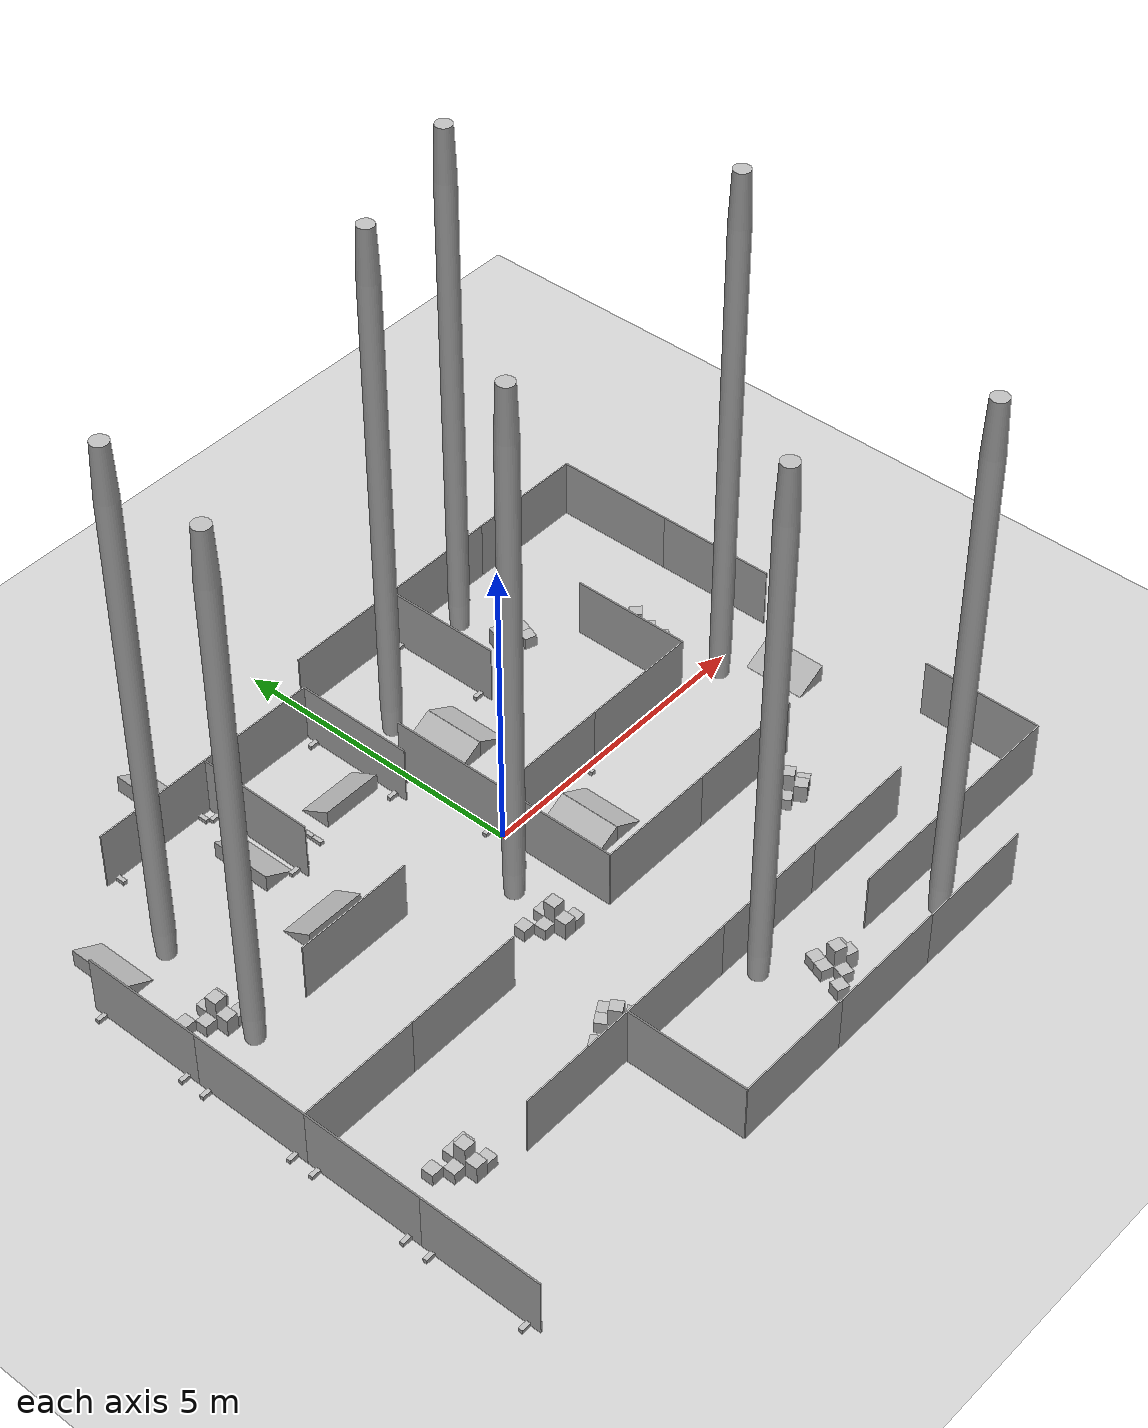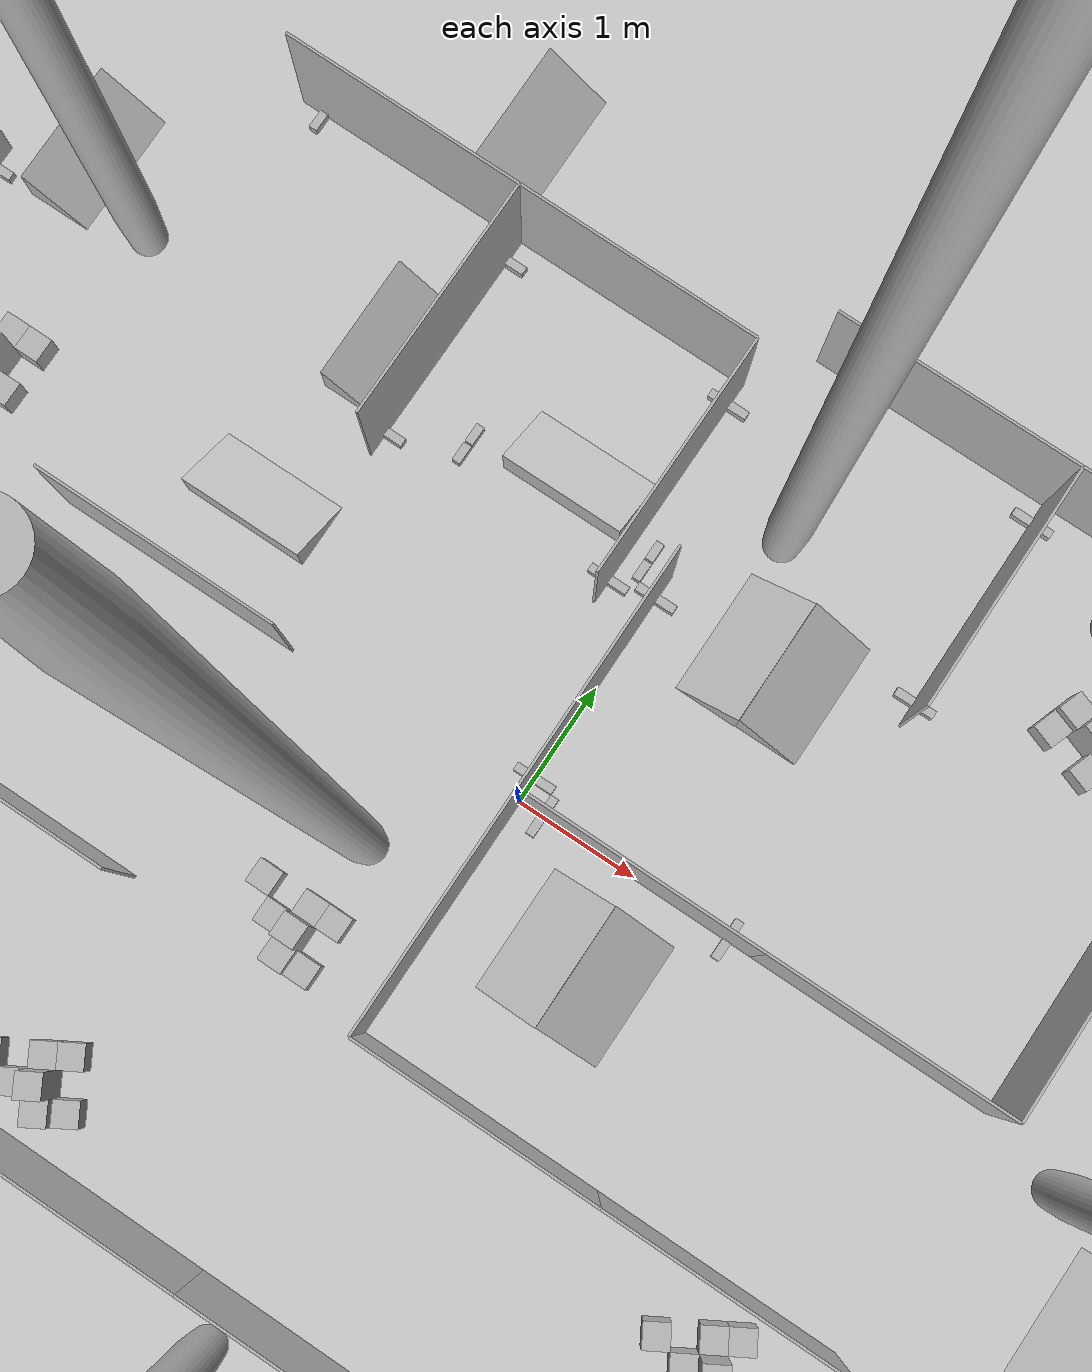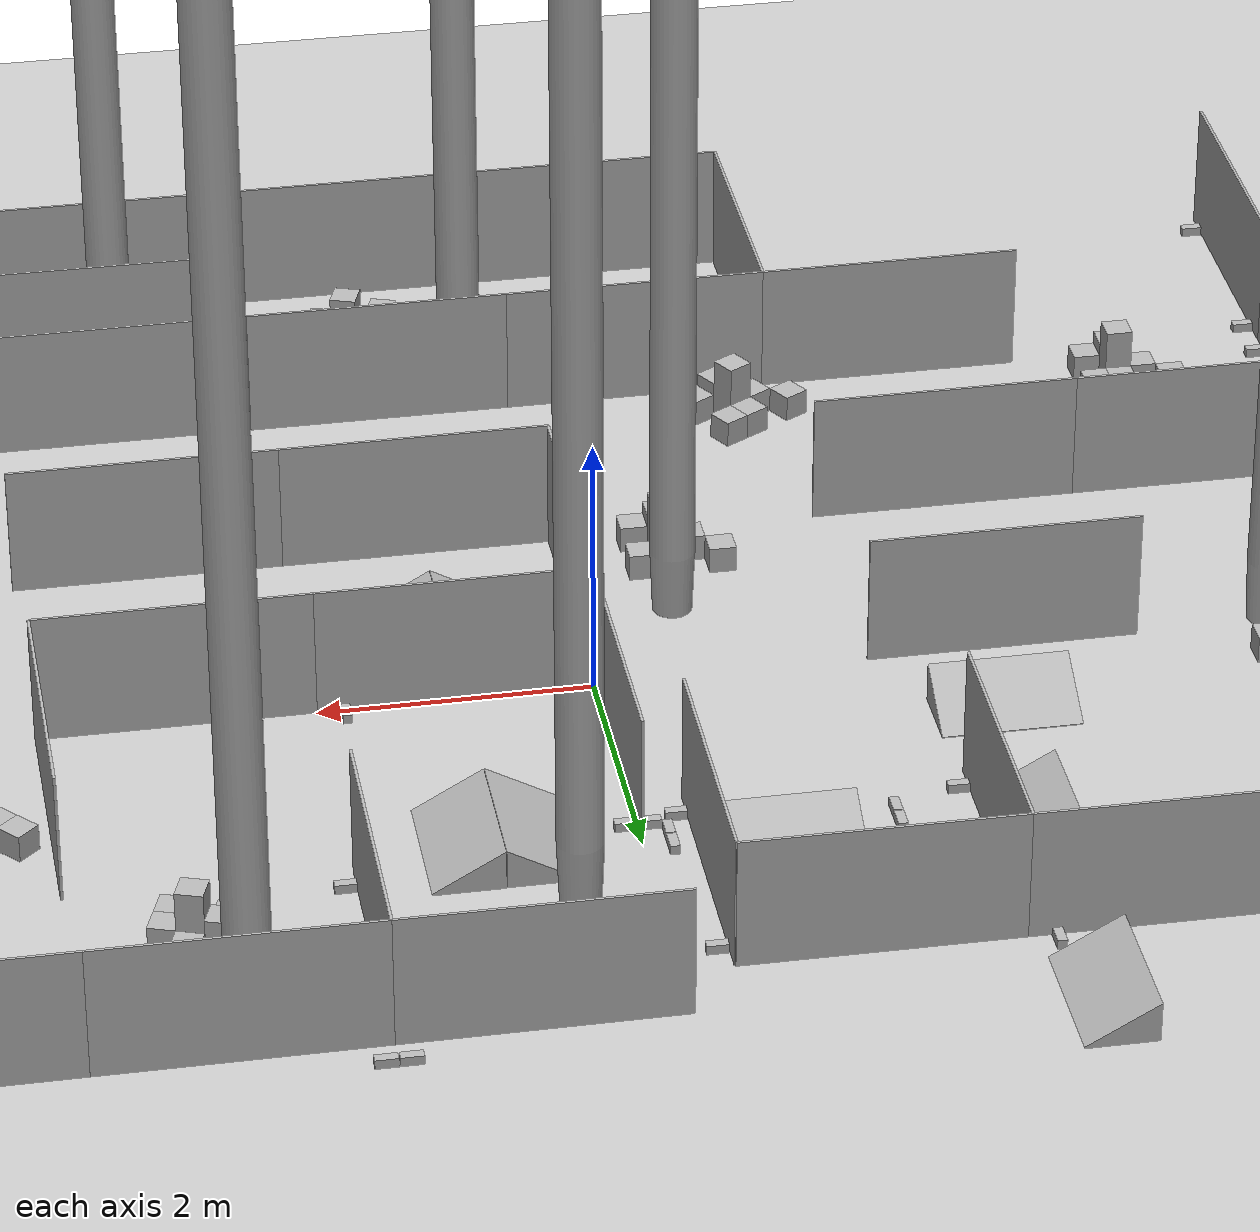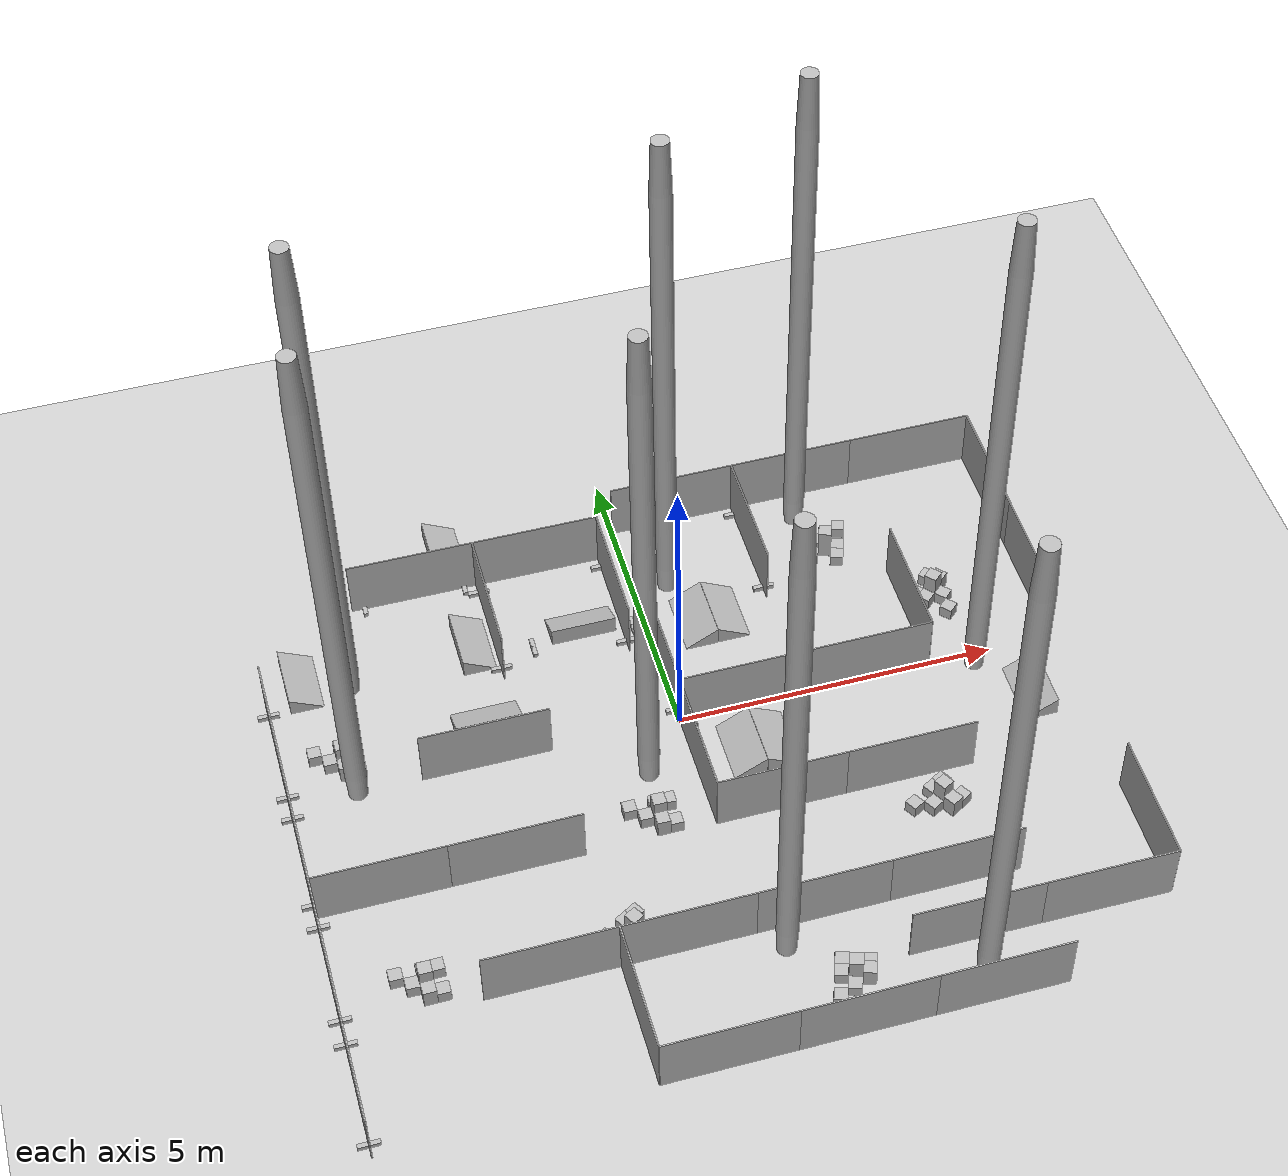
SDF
<sdf version="1.4">
  <!--Generated by blend2world.py-->
  <world name="arena_HKT_7">
    <scene>
      <ambient>0.5 0.5 0.5 1</ambient>
      <background>0.5 0.5 0.5 1</background>
      <shadows>false</shadows>
    </scene>
    <physics type="ode">
      <gravity>0 0 -9.81</gravity>
      <ode>
        <solver>
          <type>quick</type>
          <iters>1000</iters>
          <sor>1.3</sor>
        </solver>
        <constraints>
          <cfm>0.0</cfm>
          <erp>0.2</erp>
          <contact_max_correcting_vel>100.0</contact_max_correcting_vel>
          <contact_surface_layer>0.001</contact_surface_layer>
        </constraints>
      </ode>
      <real_time_update_rate>120</real_time_update_rate>
      <real_time_factor>1</real_time_factor>
      <max_step_size>0.008333</max_step_size>
    </physics>
    <light name="directional_light_1" type="directional">
      <cast_shadows>false</cast_shadows>
      <pose>0 0 30 0.1 0.1 0</pose>
      <diffuse>1.0 1.0 1.0 1</diffuse>
      <specular>.1 .1 .1 1</specular>
      <attenuation>
        <range>300</range>
      </attenuation>
      <direction>0.1 0.1 -1</direction>
    </light>
    <include>
      <uri>model://ground_plane</uri>
    </include>
    <light name="directional_light.-10.0_-12.0" type="sun">
      <pose>-10.0 -12.0 8  0 0 0</pose>
      <cast_shadows>1</cast_shadows>
      <diffuse>0.5 0.5 0.5 1</diffuse>
      <specular>0.1 0.1 0.1 1</specular>
      <attenuation>
        <range>20</range>
        <constant>0.5</constant>
        <linear>0.01</linear>
        <quadratic>0.00</quadratic>
      </attenuation>
      <direction>0.1 0.1 -1.0</direction>
    </light>
    <light name="directional_light.-10.0_0.0" type="sun">
      <pose>-10.0 0.0 8  0 0 0</pose>
      <cast_shadows>1</cast_shadows>
      <diffuse>0.5 0.5 0.5 1</diffuse>
      <specular>0.1 0.1 0.1 1</specular>
      <attenuation>
        <range>20</range>
        <constant>0.5</constant>
        <linear>0.01</linear>
        <quadratic>0.00</quadratic>
      </attenuation>
      <direction>0.1 0.1 -1.0</direction>
    </light>
    <light name="directional_light.-10.0_12.0" type="sun">
      <pose>-10.0 12.0 8  0 0 0</pose>
      <cast_shadows>1</cast_shadows>
      <diffuse>0.5 0.5 0.5 1</diffuse>
      <specular>0.1 0.1 0.1 1</specular>
      <attenuation>
        <range>20</range>
        <constant>0.5</constant>
        <linear>0.01</linear>
        <quadratic>0.00</quadratic>
      </attenuation>
      <direction>0.1 0.1 -1.0</direction>
    </light>
    <light name="directional_light.0.0_-12.0" type="sun">
      <pose>0.0 -12.0 8  0 0 0</pose>
      <cast_shadows>1</cast_shadows>
      <diffuse>0.5 0.5 0.5 1</diffuse>
      <specular>0.1 0.1 0.1 1</specular>
      <attenuation>
        <range>20</range>
        <constant>0.5</constant>
        <linear>0.01</linear>
        <quadratic>0.00</quadratic>
      </attenuation>
      <direction>0.1 0.1 -1.0</direction>
    </light>
    <light name="directional_light.0.0_0.0" type="sun">
      <pose>0.0 0.0 8  0 0 0</pose>
      <cast_shadows>1</cast_shadows>
      <diffuse>0.5 0.5 0.5 1</diffuse>
      <specular>0.1 0.1 0.1 1</specular>
      <attenuation>
        <range>20</range>
        <constant>0.5</constant>
        <linear>0.01</linear>
        <quadratic>0.00</quadratic>
      </attenuation>
      <direction>0.1 0.1 -1.0</direction>
    </light>
    <light name="directional_light.0.0_12.0" type="sun">
      <pose>0.0 12.0 8  0 0 0</pose>
      <cast_shadows>1</cast_shadows>
      <diffuse>0.5 0.5 0.5 1</diffuse>
      <specular>0.1 0.1 0.1 1</specular>
      <attenuation>
        <range>20</range>
        <constant>0.5</constant>
        <linear>0.01</linear>
        <quadratic>0.00</quadratic>
      </attenuation>
      <direction>0.1 0.1 -1.0</direction>
    </light>
    <light name="directional_light.10.0_-12.0" type="sun">
      <pose>10.0 -12.0 8  0 0 0</pose>
      <cast_shadows>1</cast_shadows>
      <diffuse>0.5 0.5 0.5 1</diffuse>
      <specular>0.1 0.1 0.1 1</specular>
      <attenuation>
        <range>20</range>
        <constant>0.5</constant>
        <linear>0.01</linear>
        <quadratic>0.00</quadratic>
      </attenuation>
      <direction>0.1 0.1 -1.0</direction>
    </light>
    <light name="directional_light.10.0_0.0" type="sun">
      <pose>10.0 0.0 8  0 0 0</pose>
      <cast_shadows>1</cast_shadows>
      <diffuse>0.5 0.5 0.5 1</diffuse>
      <specular>0.1 0.1 0.1 1</specular>
      <attenuation>
        <range>20</range>
        <constant>0.5</constant>
        <linear>0.01</linear>
        <quadratic>0.00</quadratic>
      </attenuation>
      <direction>0.1 0.1 -1.0</direction>
    </light>
    <light name="directional_light.10.0_12.0" type="sun">
      <pose>10.0 12.0 8  0 0 0</pose>
      <cast_shadows>1</cast_shadows>
      <diffuse>0.5 0.5 0.5 1</diffuse>
      <specular>0.1 0.1 0.1 1</specular>
      <attenuation>
        <range>20</range>
        <constant>0.5</constant>
        <linear>0.01</linear>
        <quadratic>0.00</quadratic>
      </attenuation>
      <direction>0.1 0.1 -1.0</direction>
    </light>
    <include>
      <name>wall_stand.794</name>
      <pose>2.0 4.19950008392334 0.03449999913573265  0.0 0.0 0.0</pose>
      <uri>model://wall_stand</uri>
    </include>
    <include>
      <name>wall_2x1.349</name>
      <pose>-5.0 -2.0 0.5130000114440918  0.0 0.0 0.0</pose>
      <uri>model://wall_2x1</uri>
    </include>
    <include>
      <name>wall_stand.795</name>
      <pose>-1.8005000352859497 2.0 0.03449999913573265  0.0 -0.0 1.570796251296997</pose>
      <uri>model://wall_stand</uri>
    </include>
    <include>
      <name>wall_stand.796</name>
      <pose>-0.19949999451637268 2.0 0.03449999913573265  0.0 -0.0 1.570796251296997</pose>
      <uri>model://wall_stand</uri>
    </include>
    <include>
      <name>wall_stand.797</name>
      <pose>-6.0 -3.80049991607666 0.03449999913573265  0.0 0.0 0.0</pose>
      <uri>model://wall_stand</uri>
    </include>
    <include>
      <name>wall_stand.798</name>
      <pose>-6.0 -2.1994998455047607 0.03449999913573265  0.0 0.0 0.0</pose>
      <uri>model://wall_stand</uri>
    </include>
    <include>
      <name>wall_2x1.350</name>
      <pose>-6.0 -3.0 0.5130000114440918  0.0 -0.0 1.570796251296997</pose>
      <uri>model://wall_2x1</uri>
    </include>
    <include>
      <name>wall_2x1.351</name>
      <pose>-6.0 -5.0 0.5130000114440918  0.0 -0.0 1.570796251296997</pose>
      <uri>model://wall_2x1</uri>
    </include>
    <include>
      <name>wall_stand.799</name>
      <pose>-6.0 -4.19950008392334 0.03449999913573265  0.0 0.0 0.0</pose>
      <uri>model://wall_stand</uri>
    </include>
    <include>
      <name>wall_stand.800</name>
      <pose>-6.0 -5.80049991607666 0.03449999913573265  0.0 0.0 0.0</pose>
      <uri>model://wall_stand</uri>
    </include>
    <include>
      <name>wall_stand.801</name>
      <pose>-6.0 -1.8004999160766602 0.03449999913573265  0.0 0.0 0.0</pose>
      <uri>model://wall_stand</uri>
    </include>
    <include>
      <name>wall_stand.802</name>
      <pose>-6.0 -0.19949984550476074 0.03449999913573265  0.0 0.0 0.0</pose>
      <uri>model://wall_stand</uri>
    </include>
    <include>
      <name>wall_2x1.352</name>
      <pose>-6.0 -1.0 0.5130000114440918  0.0 -0.0 1.570796251296997</pose>
      <uri>model://wall_2x1</uri>
    </include>
    <include>
      <name>wall_2x1.353</name>
      <pose>5.0 4.0 0.5130000114440918  0.0 0.0 0.0</pose>
      <uri>model://wall_2x1</uri>
    </include>
    <include>
      <name>wall_stand.803</name>
      <pose>-0.19949999451637268 2.0 0.03449999913573265  0.0 -0.0 1.570796251296997</pose>
      <uri>model://wall_stand</uri>
    </include>
    <include>
      <name>wall_stand.804</name>
      <pose>-1.8005000352859497 2.0 0.03449999913573265  0.0 -0.0 1.570796251296997</pose>
      <uri>model://wall_stand</uri>
    </include>
    <include>
      <name>wall_2x1.354</name>
      <pose>3.0 4.0 0.5130000114440918  0.0 0.0 0.0</pose>
      <uri>model://wall_2x1</uri>
    </include>
    <include>
      <name>wall_stand.805</name>
      <pose>-1.8005000352859497 2.0 0.03449999913573265  0.0 -0.0 1.570796251296997</pose>
      <uri>model://wall_stand</uri>
    </include>
    <include>
      <name>wall_stand.806</name>
      <pose>-0.19949999451637268 2.0 0.03449999913573265  0.0 -0.0 1.570796251296997</pose>
      <uri>model://wall_stand</uri>
    </include>
    <include>
      <name>wall_2x1.355</name>
      <pose>1.0 4.0 0.5130000114440918  0.0 0.0 0.0</pose>
      <uri>model://wall_2x1</uri>
    </include>
    <include>
      <name>wall_stand.807</name>
      <pose>-1.8005000352859497 2.0 0.03449999913573265  0.0 -0.0 1.570796251296997</pose>
      <uri>model://wall_stand</uri>
    </include>
    <include>
      <name>wall_2x1.356</name>
      <pose>1.0 -2.0 0.5130000114440918  0.0 0.0 0.0</pose>
      <uri>model://wall_2x1</uri>
    </include>
    <include>
      <name>wall_stand.808</name>
      <pose>-1.8005000352859497 2.0 0.03449999913573265  0.0 -0.0 1.570796251296997</pose>
      <uri>model://wall_stand</uri>
    </include>
    <include>
      <name>wall_stand.809</name>
      <pose>-0.19949999451637268 2.0 0.03449999913573265  0.0 -0.0 1.570796251296997</pose>
      <uri>model://wall_stand</uri>
    </include>
    <include>
      <name>wall_2x1.357</name>
      <pose>3.0 -2.0 0.5130000114440918  0.0 0.0 0.0</pose>
      <uri>model://wall_2x1</uri>
    </include>
    <include>
      <name>wall_stand.810</name>
      <pose>-0.19949999451637268 2.0 0.03449999913573265  0.0 -0.0 1.570796251296997</pose>
      <uri>model://wall_stand</uri>
    </include>
    <include>
      <name>wall_stand.811</name>
      <pose>-1.8005000352859497 2.0 0.03449999913573265  0.0 -0.0 1.570796251296997</pose>
      <uri>model://wall_stand</uri>
    </include>
    <include>
      <name>wall_2x1.358</name>
      <pose>5.965702533721924 -3.989342212677002 0.5130000114440918  0.0 -0.0 4.704471588134766</pose>
      <uri>model://wall_2x1</uri>
    </include>
    <include>
      <name>wall_stand.812</name>
      <pose>-1.8005000352859497 2.0 0.03449999913573265  0.0 -0.0 1.570796251296997</pose>
      <uri>model://wall_stand</uri>
    </include>
    <include>
      <name>wall_stand.813</name>
      <pose>-0.19949999451637268 2.0 0.03449999913573265  0.0 -0.0 1.570796251296997</pose>
      <uri>model://wall_stand</uri>
    </include>
    <include>
      <name>wall_2x1.359</name>
      <pose>4.957816123962402 -4.981392860412598 0.5130000114440918  0.0 -0.0 6.275267601013184</pose>
      <uri>model://wall_2x1</uri>
    </include>
    <include>
      <name>wall_stand.814</name>
      <pose>0.0 1.8005001544952393 0.03449999913573265  0.0 0.0 0.0</pose>
      <uri>model://wall_stand</uri>
    </include>
    <include>
      <name>wall_stand.815</name>
      <pose>0.0 0.19949999451637268 0.03449999913573265  0.0 0.0 0.0</pose>
      <uri>model://wall_stand</uri>
    </include>
    <include>
      <name>wall_2x1.360</name>
      <pose>2.957878589630127 -4.965557098388672 0.5130000114440918  0.0 -0.0 6.275267601013184</pose>
      <uri>model://wall_2x1</uri>
    </include>
    <include>
      <name>wall_stand.816</name>
      <pose>0.0 0.19949999451637268 0.03449999913573265  0.0 0.0 0.0</pose>
      <uri>model://wall_stand</uri>
    </include>
    <include>
      <name>wall_stand.817</name>
      <pose>0.0 1.8005001544952393 0.03449999913573265  0.0 0.0 0.0</pose>
      <uri>model://wall_stand</uri>
    </include>
    <include>
      <name>wall_2x1.361</name>
      <pose>-2.0 -5.0 0.5130000114440918  0.0 -0.0 1.570796251296997</pose>
      <uri>model://wall_2x1</uri>
    </include>
    <include>
      <name>wall_stand.818</name>
      <pose>0.0 0.19949999451637268 0.03449999913573265  0.0 0.0 0.0</pose>
      <uri>model://wall_stand</uri>
    </include>
    <include>
      <name>wall_stand.819</name>
      <pose>0.0 1.8005001544952393 0.03449999913573265  0.0 0.0 0.0</pose>
      <uri>model://wall_stand</uri>
    </include>
    <include>
      <name>wall_2x1.362</name>
      <pose>-1.0 -6.0 0.5130000114440918  0.0 0.0 0.0</pose>
      <uri>model://wall_2x1</uri>
    </include>
    <include>
      <name>wall_stand.820</name>
      <pose>-1.8005000352859497 2.0 0.03449999913573265  0.0 -0.0 1.570796251296997</pose>
      <uri>model://wall_stand</uri>
    </include>
    <include>
      <name>wall_stand.821</name>
      <pose>-0.19949999451637268 2.0 0.03449999913573265  0.0 -0.0 1.570796251296997</pose>
      <uri>model://wall_stand</uri>
    </include>
    <include>
      <name>wall_2x1.363</name>
      <pose>1.0 -6.0 0.5130000114440918  0.0 0.0 0.0</pose>
      <uri>model://wall_2x1</uri>
    </include>
    <include>
      <name>wall_stand.822</name>
      <pose>-0.19949999451637268 2.0 0.03449999913573265  0.0 -0.0 1.570796251296997</pose>
      <uri>model://wall_stand</uri>
    </include>
    <include>
      <name>wall_stand.823</name>
      <pose>-1.8005000352859497 2.0 0.03449999913573265  0.0 -0.0 1.570796251296997</pose>
      <uri>model://wall_stand</uri>
    </include>
    <include>
      <name>wall_2x1.364</name>
      <pose>3.0 -6.0 0.5130000114440918  0.0 0.0 0.0</pose>
      <uri>model://wall_2x1</uri>
    </include>
    <include>
      <name>wall_stand.824</name>
      <pose>-1.8005000352859497 2.0 0.03449999913573265  0.0 -0.0 1.570796251296997</pose>
      <uri>model://wall_stand</uri>
    </include>
    <include>
      <name>wall_stand.825</name>
      <pose>-0.19949999451637268 2.0 0.03449999913573265  0.0 -0.0 1.570796251296997</pose>
      <uri>model://wall_stand</uri>
    </include>
    <include>
      <name>wall_2x1.365</name>
      <pose>6.0 1.0 0.5130000114440918  0.0 -0.0 1.570796251296997</pose>
      <uri>model://wall_2x1</uri>
    </include>
    <include>
      <name>wall_stand.826</name>
      <pose>0.0 1.8005001544952393 0.03449999913573265  0.0 0.0 0.0</pose>
      <uri>model://wall_stand</uri>
    </include>
    <include>
      <name>wall_stand.827</name>
      <pose>0.0 0.19949999451637268 0.03449999913573265  0.0 0.0 0.0</pose>
      <uri>model://wall_stand</uri>
    </include>
    <include>
      <name>wall_2x1.366</name>
      <pose>6.0 3.0 0.5130000114440918  0.0 -0.0 1.570796251296997</pose>
      <uri>model://wall_2x1</uri>
    </include>
    <include>
      <name>wall_stand.828</name>
      <pose>0.0 0.19949999451637268 0.03449999913573265  0.0 0.0 0.0</pose>
      <uri>model://wall_stand</uri>
    </include>
    <include>
      <name>wall_stand.829</name>
      <pose>0.0 1.8005001544952393 0.03449999913573265  0.0 0.0 0.0</pose>
      <uri>model://wall_stand</uri>
    </include>
    <include>
      <name>wall_stand.830</name>
      <pose>0.0 0.19949999451637268 0.03449999913573265  0.0 0.0 0.0</pose>
      <uri>model://wall_stand</uri>
    </include>
    <include>
      <name>wall_stand.831</name>
      <pose>-2.55926251411438 3.5389766693115234 0.03450000286102295  0.0 -0.0 4.707121849060059</pose>
      <uri>model://wall_stand</uri>
    </include>
    <include>
      <name>wall_stand.832</name>
      <pose>-4.160240173339844 3.5474095344543457 0.03450000286102295  0.0 -0.0 4.707121849060059</pose>
      <uri>model://wall_stand</uri>
    </include>
    <include>
      <name>wall_stand.833</name>
      <pose>-0.19949999451637268 2.0 0.03449999913573265  0.0 -0.0 1.570796251296997</pose>
      <uri>model://wall_stand</uri>
    </include>
    <include>
      <name>wall_stand.834</name>
      <pose>0.0 1.8005001544952393 0.03449999913573265  0.0 0.0 0.0</pose>
      <uri>model://wall_stand</uri>
    </include>
    <include>
      <name>wall_stand.835</name>
      <pose>0.0 0.19949999451637268 0.03449999913573265  0.0 0.0 0.0</pose>
      <uri>model://wall_stand</uri>
    </include>
    <include>
      <name>wall_stand.836</name>
      <pose>-2.55926251411438 3.5389766693115234 0.03450000286102295  0.0 -0.0 4.707121849060059</pose>
      <uri>model://wall_stand</uri>
    </include>
    <include>
      <name>wall_2x1.367</name>
      <pose>0.0 -1.0 0.5130000114440918  0.0 -0.0 1.570796251296997</pose>
      <uri>model://wall_2x1</uri>
    </include>
    <include>
      <name>wall_stand.837</name>
      <pose>0.0 0.19949999451637268 0.03449999913573265  0.0 0.0 0.0</pose>
      <uri>model://wall_stand</uri>
    </include>
    <include>
      <name>wall_stand.838</name>
      <pose>0.0 1.8005001544952393 0.03449999913573265  0.0 0.0 0.0</pose>
      <uri>model://wall_stand</uri>
    </include>
    <include>
      <name>wall_2x1.368</name>
      <pose>3.0 -4.0 0.5130000114440918  0.0 0.0 0.0</pose>
      <uri>model://wall_2x1</uri>
    </include>
    <include>
      <name>wall_stand.839</name>
      <pose>-0.19949999451637268 2.0 0.03449999913573265  0.0 -0.0 1.570796251296997</pose>
      <uri>model://wall_stand</uri>
    </include>
    <include>
      <name>wall_stand.840</name>
      <pose>-1.8005000352859497 2.0 0.03449999913573265  0.0 -0.0 1.570796251296997</pose>
      <uri>model://wall_stand</uri>
    </include>
    <include>
      <name>wall_2x1.369</name>
      <pose>1.0 -4.0 0.5130000114440918  0.0 0.0 0.0</pose>
      <uri>model://wall_2x1</uri>
    </include>
    <include>
      <name>wall_stand.841</name>
      <pose>-1.8005000352859497 2.0 0.03449999913573265  0.0 -0.0 1.570796251296997</pose>
      <uri>model://wall_stand</uri>
    </include>
    <include>
      <name>wall_stand.842</name>
      <pose>-0.19949999451637268 2.0 0.03449999913573265  0.0 -0.0 1.570796251296997</pose>
      <uri>model://wall_stand</uri>
    </include>
    <include>
      <name>wall_2x1.370</name>
      <pose>-1.0 -4.0 0.5130000114440918  0.0 0.0 0.0</pose>
      <uri>model://wall_2x1</uri>
    </include>
    <include>
      <name>wall_stand.843</name>
      <pose>-0.19949999451637268 2.0 0.03449999913573265  0.0 -0.0 1.570796251296997</pose>
      <uri>model://wall_stand</uri>
    </include>
    <include>
      <name>wall_stand.844</name>
      <pose>-1.8005000352859497 2.0 0.03449999913573265  0.0 -0.0 1.570796251296997</pose>
      <uri>model://wall_stand</uri>
    </include>
    <include>
      <name>wall_2x1.371</name>
      <pose>-3.0 -4.0 0.5130000114440918  0.0 0.0 0.0</pose>
      <uri>model://wall_2x1</uri>
    </include>
    <include>
      <name>wall_stand.845</name>
      <pose>-1.8005000352859497 2.0 0.03449999913573265  0.0 -0.0 1.570796251296997</pose>
      <uri>model://wall_stand</uri>
    </include>
    <include>
      <name>wall_stand.846</name>
      <pose>-0.19949999451637268 2.0 0.03449999913573265  0.0 -0.0 1.570796251296997</pose>
      <uri>model://wall_stand</uri>
    </include>
    <include>
      <name>wall_2x1.372</name>
      <pose>-3.0 -2.0 0.5130000114440918  0.0 0.0 0.0</pose>
      <uri>model://wall_2x1</uri>
    </include>
    <include>
      <name>wall_stand.847</name>
      <pose>-0.19949999451637268 2.0 0.03449999913573265  0.0 -0.0 1.570796251296997</pose>
      <uri>model://wall_stand</uri>
    </include>
    <include>
      <name>wall_stand.848</name>
      <pose>-1.8005000352859497 2.0 0.03449999913573265  0.0 -0.0 1.570796251296997</pose>
      <uri>model://wall_stand</uri>
    </include>
    <include>
      <name>wall_2x1.373</name>
      <pose>3.0 0.0 0.5130000114440918  0.0 0.0 0.0</pose>
      <uri>model://wall_2x1</uri>
    </include>
    <include>
      <name>wall_stand.849</name>
      <pose>0.19949999451637268 0.0 0.03449999913573265  0.0 -0.0 1.570796251296997</pose>
      <uri>model://wall_stand</uri>
    </include>
    <include>
      <name>wall_stand.850</name>
      <pose>1.8005000352859497 0.0 0.03449999913573265  0.0 -0.0 1.570796251296997</pose>
      <uri>model://wall_stand</uri>
    </include>
    <include>
      <name>wall_2x1.374</name>
      <pose>4.0 1.0 0.5130000114440918  0.0 -0.0 1.570796251296997</pose>
      <uri>model://wall_2x1</uri>
    </include>
    <include>
      <name>wall_stand.851</name>
      <pose>0.0 0.19949999451637268 0.03449999913573265  0.0 0.0 0.0</pose>
      <uri>model://wall_stand</uri>
    </include>
    <include>
      <name>wall_stand.852</name>
      <pose>0.0 1.8005001544952393 0.03449999913573265  0.0 0.0 0.0</pose>
      <uri>model://wall_stand</uri>
    </include>
    <include>
      <name>wall_2x1.375</name>
      <pose>-3.0 0.0 0.5130000114440918  0.0 0.0 0.0</pose>
      <uri>model://wall_2x1</uri>
    </include>
    <include>
      <name>wall_stand.853</name>
      <pose>-1.8005000352859497 2.0 0.03449999913573265  0.0 -0.0 1.570796251296997</pose>
      <uri>model://wall_stand</uri>
    </include>
    <include>
      <name>wall_stand.854</name>
      <pose>-0.19949999451637268 2.0 0.03449999913573265  0.0 -0.0 1.570796251296997</pose>
      <uri>model://wall_stand</uri>
    </include>
    <include>
      <name>wall_2x1.376</name>
      <pose>-1.3597792387008667 3.532658576965332 0.5130000114440918  0.0 -0.0 3.1363253593444824</pose>
      <uri>model://wall_2x1</uri>
    </include>
    <include>
      <name>wall_stand.855</name>
      <pose>-0.19949999451637268 2.0 0.03449999913573265  0.0 -0.0 1.570796251296997</pose>
      <uri>model://wall_stand</uri>
    </include>
    <include>
      <name>wall_stand.856</name>
      <pose>-1.8005000352859497 2.0 0.03449999913573265  0.0 -0.0 1.570796251296997</pose>
      <uri>model://wall_stand</uri>
    </include>
    <include>
      <name>cube_20x20.911</name>
      <pose>-0.800000011920929 -1.470605492591858 0.10000000149011612  0.0 -0.0 3.141592502593994</pose>
      <uri>model://cube_20x20</uri>
    </include>
    <include>
      <name>cube_20x20.912</name>
      <pose>-1.0 -1.6706054210662842 0.10000000149011612  0.0 -0.0 3.141592502593994</pose>
      <uri>model://cube_20x20</uri>
    </include>
    <include>
      <name>cube_20x20.913</name>
      <pose>-1.2000000476837158 -1.470605492591858 0.10000000149011612  0.0 -0.0 3.141592502593994</pose>
      <uri>model://cube_20x20</uri>
    </include>
    <include>
      <name>cube_20x20.914</name>
      <pose>-0.6000000238418579 -1.470605492591858 0.10000000149011612  0.0 -0.0 3.141592502593994</pose>
      <uri>model://cube_20x20</uri>
    </include>
    <include>
      <name>cube_20x20.915</name>
      <pose>-0.6000000238418579 -1.87060546875 0.10000000149011612  0.0 -0.0 3.141592502593994</pose>
      <uri>model://cube_20x20</uri>
    </include>
    <include>
      <name>cube_20x30.151</name>
      <pose>-0.800000011920929 -1.87060546875 0.15000000596046448  0.0 -0.0 3.141592502593994</pose>
      <uri>model://cube_20x30</uri>
    </include>
    <include>
      <name>cube_20x50.145</name>
      <pose>-0.800000011920929 -1.6706054210662842 0.25  0.0 -0.0 3.141592502593994</pose>
      <uri>model://cube_20x50</uri>
    </include>
    <include>
      <name>ramp.050</name>
      <pose>5.316980361938477 -0.9300249814987183 0.15000000596046448  0.0 -0.0 9.416860580444336</pose>
      <uri>model://ramp</uri>
    </include>
    <include>
      <name>ramp.061</name>
      <pose>-0.9832800030708313 2.2666399478912354 0.15000000596046448  0.0 -0.0 7.853981971740723</pose>
      <uri>model://ramp</uri>
    </include>
    <include>
      <name>wall_2x1.377</name>
      <pose>1.0 0.0 0.5130000114440918  0.0 0.0 0.0</pose>
      <uri>model://wall_2x1</uri>
    </include>
    <include>
      <name>wall_stand.857</name>
      <pose>1.8005000352859497 0.0 0.03449999913573265  0.0 -0.0 1.570796251296997</pose>
      <uri>model://wall_stand</uri>
    </include>
    <include>
      <name>wall_stand.858</name>
      <pose>0.19949999451637268 0.0 0.03449999913573265  0.0 -0.0 1.570796251296997</pose>
      <uri>model://wall_stand</uri>
    </include>
    <include>
      <name>wall_2x1.378</name>
      <pose>0.0 1.0 0.5130000114440918  0.0 -0.0 1.570796251296997</pose>
      <uri>model://wall_2x1</uri>
    </include>
    <include>
      <name>wall_stand.859</name>
      <pose>0.0 1.8005001544952393 0.03449999913573265  0.0 0.0 0.0</pose>
      <uri>model://wall_stand</uri>
    </include>
    <include>
      <name>wall_stand.860</name>
      <pose>0.0 0.19949999451637268 0.03449999913573265  0.0 0.0 0.0</pose>
      <uri>model://wall_stand</uri>
    </include>
    <include>
      <name>wall_2x1.379</name>
      <pose>-0.36506032943725586 2.527405261993408 0.5130000114440918  0.0 -0.0 4.707121849060059</pose>
      <uri>model://wall_2x1</uri>
    </include>
    <include>
      <name>wall_2x1.380</name>
      <pose>-2.36503267288208 2.53794002532959 0.5130000114440918  0.0 -0.0 4.707121849060059</pose>
      <uri>model://wall_2x1</uri>
    </include>
    <include>
      <name>wall_2x1.381</name>
      <pose>-6.0 1.0 0.5130000114440918  0.0 -0.0 1.570796251296997</pose>
      <uri>model://wall_2x1</uri>
    </include>
    <include>
      <name>wall_2x1.382</name>
      <pose>2.0 3.0 0.5130000114440918  0.0 -0.0 1.570796251296997</pose>
      <uri>model://wall_2x1</uri>
    </include>
    <include>
      <name>wall_2x1.383</name>
      <pose>-3.3597514629364014 3.5431928634643555 0.5130000114440918  0.0 -0.0 3.1363253593444824</pose>
      <uri>model://wall_2x1</uri>
    </include>
    <include>
      <name>wall_stand.861</name>
      <pose>-1.8005000352859497 2.0 0.03449999913573265  0.0 -0.0 1.570796251296997</pose>
      <uri>model://wall_stand</uri>
    </include>
    <include>
      <name>wall_stand.862</name>
      <pose>-0.19949999451637268 2.0 0.03449999913573265  0.0 -0.0 1.570796251296997</pose>
      <uri>model://wall_stand</uri>
    </include>
    <include>
      <name>wall_stand.863</name>
      <pose>-0.36084413528442383 3.3278937339782715 0.03450000286102295  0.0 -0.0 3.1363253593444824</pose>
      <uri>model://wall_stand</uri>
    </include>
    <include>
      <name>wall_stand.864</name>
      <pose>2.0 2.19950008392334 0.03449999913573265  0.0 0.0 0.0</pose>
      <uri>model://wall_stand</uri>
    </include>
    <include>
      <name>wall_stand.865</name>
      <pose>-2.360816240310669 3.338428497314453 0.03450000286102295  0.0 -0.0 3.1363253593444824</pose>
      <uri>model://wall_stand</uri>
    </include>
    <include>
      <name>wall_stand.866</name>
      <pose>2.0 3.817974328994751 0.03449999913573265  0.0 0.0 0.0</pose>
      <uri>model://wall_stand</uri>
    </include>
    <include>
      <name>wall_stand.867</name>
      <pose>-2.369249105453491 1.7374505996704102 0.03450000286102295  0.0 -0.0 3.1363253593444824</pose>
      <uri>model://wall_stand</uri>
    </include>
    <include>
      <name>wall_stand.868</name>
      <pose>-6.0 1.8005001544952393 0.03449999913573265  0.0 0.0 0.0</pose>
      <uri>model://wall_stand</uri>
    </include>
    <include>
      <name>wall_stand.869</name>
      <pose>-6.0 0.19950008392333984 0.03449999913573265  0.0 0.0 0.0</pose>
      <uri>model://wall_stand</uri>
    </include>
    <include>
      <name>wall_stand.870</name>
      <pose>-0.3692770004272461 1.7269160747528076 0.03450000286102295  0.0 -0.0 3.1363253593444824</pose>
      <uri>model://wall_stand</uri>
    </include>
    <include>
      <name>cube_20x20.916</name>
      <pose>-5.073810577392578 0.8086726665496826 0.10000000149011612  0.0 -0.0 3.141592502593994</pose>
      <uri>model://cube_20x20</uri>
    </include>
    <include>
      <name>cube_20x20.917</name>
      <pose>-5.273810386657715 0.6086728572845459 0.10000000149011612  0.0 -0.0 3.141592502593994</pose>
      <uri>model://cube_20x20</uri>
    </include>
    <include>
      <name>cube_20x20.918</name>
      <pose>-5.473810195922852 0.8086726665496826 0.10000000149011612  0.0 -0.0 3.141592502593994</pose>
      <uri>model://cube_20x20</uri>
    </include>
    <include>
      <name>cube_20x20.919</name>
      <pose>-4.873810291290283 0.8086726665496826 0.10000000149011612  0.0 -0.0 3.141592502593994</pose>
      <uri>model://cube_20x20</uri>
    </include>
    <include>
      <name>cube_20x20.920</name>
      <pose>-4.873810291290283 0.4086730480194092 0.10000000149011612  0.0 -0.0 3.141592502593994</pose>
      <uri>model://cube_20x20</uri>
    </include>
    <include>
      <name>cube_20x20.921</name>
      <pose>-5.073810577392578 0.8086726665496826 0.10000000149011612  0.0 -0.0 3.141592502593994</pose>
      <uri>model://cube_20x20</uri>
    </include>
    <include>
      <name>cube_20x20.922</name>
      <pose>-5.273810386657715 0.6086728572845459 0.10000000149011612  0.0 -0.0 3.141592502593994</pose>
      <uri>model://cube_20x20</uri>
    </include>
    <include>
      <name>cube_20x20.923</name>
      <pose>-5.473810195922852 0.8086726665496826 0.10000000149011612  0.0 -0.0 3.141592502593994</pose>
      <uri>model://cube_20x20</uri>
    </include>
    <include>
      <name>cube_20x20.924</name>
      <pose>-4.873810291290283 0.8086726665496826 0.10000000149011612  0.0 -0.0 3.141592502593994</pose>
      <uri>model://cube_20x20</uri>
    </include>
    <include>
      <name>cube_20x20.925</name>
      <pose>-4.873810291290283 0.4086730480194092 0.10000000149011612  0.0 -0.0 3.141592502593994</pose>
      <uri>model://cube_20x20</uri>
    </include>
    <include>
      <name>cube_20x20.926</name>
      <pose>-4.71690034866333 -3.3630831241607666 0.10000000149011612  0.0 -0.0 3.141592502593994</pose>
      <uri>model://cube_20x20</uri>
    </include>
    <include>
      <name>cube_20x20.927</name>
      <pose>-4.916900157928467 -3.5630829334259033 0.10000000149011612  0.0 -0.0 3.141592502593994</pose>
      <uri>model://cube_20x20</uri>
    </include>
    <include>
      <name>cube_20x20.928</name>
      <pose>-5.1168999671936035 -3.3630831241607666 0.10000000149011612  0.0 -0.0 3.141592502593994</pose>
      <uri>model://cube_20x20</uri>
    </include>
    <include>
      <name>cube_20x20.929</name>
      <pose>-4.516900062561035 -3.3630831241607666 0.10000000149011612  0.0 -0.0 3.141592502593994</pose>
      <uri>model://cube_20x20</uri>
    </include>
    <include>
      <name>cube_20x20.930</name>
      <pose>-4.516900062561035 -3.76308274269104 0.10000000149011612  0.0 -0.0 3.141592502593994</pose>
      <uri>model://cube_20x20</uri>
    </include>
    <include>
      <name>cube_20x20.931</name>
      <pose>-4.71690034866333 -3.3630831241607666 0.10000000149011612  0.0 -0.0 3.141592502593994</pose>
      <uri>model://cube_20x20</uri>
    </include>
    <include>
      <name>cube_20x20.932</name>
      <pose>-4.916900157928467 -3.5630829334259033 0.10000000149011612  0.0 -0.0 3.141592502593994</pose>
      <uri>model://cube_20x20</uri>
    </include>
    <include>
      <name>cube_20x20.933</name>
      <pose>-5.1168999671936035 -3.3630831241607666 0.10000000149011612  0.0 -0.0 3.141592502593994</pose>
      <uri>model://cube_20x20</uri>
    </include>
    <include>
      <name>cube_20x20.934</name>
      <pose>-4.516900062561035 -3.3630831241607666 0.10000000149011612  0.0 -0.0 3.141592502593994</pose>
      <uri>model://cube_20x20</uri>
    </include>
    <include>
      <name>cube_20x20.935</name>
      <pose>-4.516900062561035 -3.76308274269104 0.10000000149011612  0.0 -0.0 3.141592502593994</pose>
      <uri>model://cube_20x20</uri>
    </include>
    <include>
      <name>cube_20x20.936</name>
      <pose>-1.7805752754211426 -3.3717634677886963 0.10000000149011612  0.0 -0.0 3.6651763916015625</pose>
      <uri>model://cube_20x20</uri>
    </include>
    <include>
      <name>cube_20x20.937</name>
      <pose>-1.8537843227386475 -3.6449673175811768 0.10000000149011612  0.0 -0.0 3.6651763916015625</pose>
      <uri>model://cube_20x20</uri>
    </include>
    <include>
      <name>cube_20x20.938</name>
      <pose>-2.126988172531128 -3.5717580318450928 0.10000000149011612  0.0 -0.0 3.6651763916015625</pose>
      <uri>model://cube_20x20</uri>
    </include>
    <include>
      <name>cube_20x20.939</name>
      <pose>-1.6073683500289917 -3.271765947341919 0.10000000149011612  0.0 -0.0 3.6651763916015625</pose>
      <uri>model://cube_20x20</uri>
    </include>
    <include>
      <name>cube_20x20.940</name>
      <pose>-1.4073739051818848 -3.6181790828704834 0.10000000149011612  0.0 -0.0 3.6651763916015625</pose>
      <uri>model://cube_20x20</uri>
    </include>
    <include>
      <name>cube_20x20.941</name>
      <pose>-1.7805752754211426 -3.3717634677886963 0.10000000149011612  0.0 -0.0 3.6651763916015625</pose>
      <uri>model://cube_20x20</uri>
    </include>
    <include>
      <name>cube_20x20.942</name>
      <pose>-1.8537843227386475 -3.6449673175811768 0.10000000149011612  0.0 -0.0 3.6651763916015625</pose>
      <uri>model://cube_20x20</uri>
    </include>
    <include>
      <name>cube_20x20.943</name>
      <pose>-2.126988172531128 -3.5717580318450928 0.10000000149011612  0.0 -0.0 3.6651763916015625</pose>
      <uri>model://cube_20x20</uri>
    </include>
    <include>
      <name>cube_20x20.944</name>
      <pose>-1.6073683500289917 -3.271765947341919 0.10000000149011612  0.0 -0.0 3.6651763916015625</pose>
      <uri>model://cube_20x20</uri>
    </include>
    <include>
      <name>cube_20x20.945</name>
      <pose>-1.4073739051818848 -3.6181790828704834 0.10000000149011612  0.0 -0.0 3.6651763916015625</pose>
      <uri>model://cube_20x20</uri>
    </include>
    <include>
      <name>cube_20x20.946</name>
      <pose>4.368031978607178 1.1892588138580322 0.10000000149011612  0.0 0.0 5.4528021812438965</pose>
      <uri>model://cube_20x20</uri>
    </include>
    <include>
      <name>cube_20x20.947</name>
      <pose>4.650588035583496 1.176539659500122 0.10000000149011612  0.0 0.0 5.4528021812438965</pose>
      <uri>model://cube_20x20</uri>
    </include>
    <include>
      <name>cube_20x20.948</name>
      <pose>4.637868404388428 0.8939831256866455 0.10000000149011612  0.0 0.0 5.4528021812438965</pose>
      <uri>model://cube_20x20</uri>
    </include>
    <include>
      <name>cube_20x20.949</name>
      <pose>4.2331132888793945 1.3368971347808838 0.10000000149011612  0.0 0.0 5.4528021812438965</pose>
      <uri>model://cube_20x20</uri>
    </include>
    <include>
      <name>cube_20x20.950</name>
      <pose>4.5283894538879395 1.6067335605621338 0.10000000149011612  0.0 0.0 5.4528021812438965</pose>
      <uri>model://cube_20x20</uri>
    </include>
    <include>
      <name>cube_20x20.951</name>
      <pose>4.368031978607178 1.1892588138580322 0.10000000149011612  0.0 0.0 5.4528021812438965</pose>
      <uri>model://cube_20x20</uri>
    </include>
    <include>
      <name>cube_20x20.952</name>
      <pose>4.650588035583496 1.176539659500122 0.10000000149011612  0.0 0.0 5.4528021812438965</pose>
      <uri>model://cube_20x20</uri>
    </include>
    <include>
      <name>cube_20x20.953</name>
      <pose>4.637868404388428 0.8939831256866455 0.10000000149011612  0.0 0.0 5.4528021812438965</pose>
      <uri>model://cube_20x20</uri>
    </include>
    <include>
      <name>cube_20x20.954</name>
      <pose>4.2331132888793945 1.3368971347808838 0.10000000149011612  0.0 0.0 5.4528021812438965</pose>
      <uri>model://cube_20x20</uri>
    </include>
    <include>
      <name>cube_20x20.955</name>
      <pose>4.5283894538879395 1.6067335605621338 0.10000000149011612  0.0 0.0 5.4528021812438965</pose>
      <uri>model://cube_20x20</uri>
    </include>
    <include>
      <name>cube_20x20.956</name>
      <pose>3.3604865074157715 2.6194584369659424 0.10000000149011612  0.0 0.0 7.517675399780273</pose>
      <uri>model://cube_20x20</uri>
    </include>
    <include>
      <name>cube_20x20.957</name>
      <pose>3.2376906871795654 2.8742544651031494 0.10000000149011612  0.0 0.0 7.517675399780273</pose>
      <uri>model://cube_20x20</uri>
    </include>
    <include>
      <name>cube_20x20.958</name>
      <pose>3.4924871921539307 2.9970500469207764 0.10000000149011612  0.0 0.0 7.517675399780273</pose>
      <uri>model://cube_20x20</uri>
    </include>
    <include>
      <name>cube_20x20.959</name>
      <pose>3.294485569000244 2.4306623935699463 0.10000000149011612  0.0 0.0 7.517675399780273</pose>
      <uri>model://cube_20x20</uri>
    </include>
    <include>
      <name>cube_20x20.960</name>
      <pose>2.91689395904541 2.5626633167266846 0.10000000149011612  0.0 0.0 7.517675399780273</pose>
      <uri>model://cube_20x20</uri>
    </include>
    <include>
      <name>cube_20x20.961</name>
      <pose>3.3604865074157715 2.6194584369659424 0.10000000149011612  0.0 0.0 7.517675399780273</pose>
      <uri>model://cube_20x20</uri>
    </include>
    <include>
      <name>cube_20x20.962</name>
      <pose>3.2376906871795654 2.8742544651031494 0.10000000149011612  0.0 0.0 7.517675399780273</pose>
      <uri>model://cube_20x20</uri>
    </include>
    <include>
      <name>cube_20x20.963</name>
      <pose>3.4924871921539307 2.9970500469207764 0.10000000149011612  0.0 0.0 7.517675399780273</pose>
      <uri>model://cube_20x20</uri>
    </include>
    <include>
      <name>cube_20x20.964</name>
      <pose>3.294485569000244 2.4306623935699463 0.10000000149011612  0.0 0.0 7.517675399780273</pose>
      <uri>model://cube_20x20</uri>
    </include>
    <include>
      <name>cube_20x20.965</name>
      <pose>2.91689395904541 2.5626633167266846 0.10000000149011612  0.0 0.0 7.517675399780273</pose>
      <uri>model://cube_20x20</uri>
    </include>
    <include>
      <name>cube_20x20.966</name>
      <pose>3.2194247245788574 -2.3717634677886963 0.10000000149011612  0.0 -0.0 3.6651763916015625</pose>
      <uri>model://cube_20x20</uri>
    </include>
    <include>
      <name>cube_20x20.967</name>
      <pose>2.873011827468872 -2.5717580318450928 0.10000000149011612  0.0 -0.0 3.6651763916015625</pose>
      <uri>model://cube_20x20</uri>
    </include>
    <include>
      <name>cube_20x20.968</name>
      <pose>3.3926315307617188 -2.271765947341919 0.10000000149011612  0.0 -0.0 3.6651763916015625</pose>
      <uri>model://cube_20x20</uri>
    </include>
    <include>
      <name>cube_20x20.969</name>
      <pose>3.5926260948181152 -2.6181790828704834 0.10000000149011612  0.0 -0.0 3.6651763916015625</pose>
      <uri>model://cube_20x20</uri>
    </include>
    <include>
      <name>cube_20x20.970</name>
      <pose>3.2194247245788574 -2.3717634677886963 0.10000000149011612  0.0 -0.0 3.6651763916015625</pose>
      <uri>model://cube_20x20</uri>
    </include>
    <include>
      <name>cube_20x20.971</name>
      <pose>3.1462156772613525 -2.6449673175811768 0.10000000149011612  0.0 -0.0 3.6651763916015625</pose>
      <uri>model://cube_20x20</uri>
    </include>
    <include>
      <name>cube_20x20.972</name>
      <pose>2.873011827468872 -2.5717580318450928 0.10000000149011612  0.0 -0.0 3.6651763916015625</pose>
      <uri>model://cube_20x20</uri>
    </include>
    <include>
      <name>cube_20x20.973</name>
      <pose>3.3926315307617188 -2.271765947341919 0.10000000149011612  0.0 -0.0 3.6651763916015625</pose>
      <uri>model://cube_20x20</uri>
    </include>
    <include>
      <name>cube_20x20.974</name>
      <pose>3.5926260948181152 -2.6181790828704834 0.10000000149011612  0.0 -0.0 3.6651763916015625</pose>
      <uri>model://cube_20x20</uri>
    </include>
    <include>
      <name>cube_20x20.975</name>
      <pose>0.9221256971359253 -5.038193702697754 0.10000000149011612  0.0 0.0 4.376082897186279</pose>
      <uri>model://cube_20x20</uri>
    </include>
    <include>
      <name>cube_20x20.976</name>
      <pose>1.0449215173721313 -5.292989730834961 0.10000000149011612  0.0 0.0 4.376082897186279</pose>
      <uri>model://cube_20x20</uri>
    </include>
    <include>
      <name>cube_20x20.977</name>
      <pose>0.7901250123977661 -5.415785789489746 0.10000000149011612  0.0 0.0 4.376082897186279</pose>
      <uri>model://cube_20x20</uri>
    </include>
    <include>
      <name>cube_20x20.978</name>
      <pose>0.9881266355514526 -4.849397659301758 0.10000000149011612  0.0 0.0 4.376082897186279</pose>
      <uri>model://cube_20x20</uri>
    </include>
    <include>
      <name>cube_20x20.979</name>
      <pose>1.3657182455062866 -4.981398582458496 0.10000000149011612  0.0 0.0 4.376082897186279</pose>
      <uri>model://cube_20x20</uri>
    </include>
    <include>
      <name>cube_20x20.980</name>
      <pose>0.9221256971359253 -5.038193702697754 0.10000000149011612  0.0 0.0 4.376082897186279</pose>
      <uri>model://cube_20x20</uri>
    </include>
    <include>
      <name>cube_20x20.981</name>
      <pose>1.0449215173721313 -5.292989730834961 0.10000000149011612  0.0 0.0 4.376082897186279</pose>
      <uri>model://cube_20x20</uri>
    </include>
    <include>
      <name>cube_20x20.982</name>
      <pose>0.7901250123977661 -5.415785789489746 0.10000000149011612  0.0 0.0 4.376082897186279</pose>
      <uri>model://cube_20x20</uri>
    </include>
    <include>
      <name>cube_20x20.983</name>
      <pose>0.9881266355514526 -4.849397659301758 0.10000000149011612  0.0 0.0 4.376082897186279</pose>
      <uri>model://cube_20x20</uri>
    </include>
    <include>
      <name>cube_20x20.984</name>
      <pose>1.3657182455062866 -4.981398582458496 0.10000000149011612  0.0 0.0 4.376082897186279</pose>
      <uri>model://cube_20x20</uri>
    </include>
    <include>
      <name>cube_20x30.152</name>
      <pose>-5.073810577392578 0.4086730480194092 0.15000000596046448  0.0 -0.0 3.141592502593994</pose>
      <uri>model://cube_20x30</uri>
    </include>
    <include>
      <name>cube_20x30.153</name>
      <pose>-5.073810577392578 0.4086730480194092 0.15000000596046448  0.0 -0.0 3.141592502593994</pose>
      <uri>model://cube_20x30</uri>
    </include>
    <include>
      <name>cube_20x30.154</name>
      <pose>-4.71690034866333 -3.76308274269104 0.15000000596046448  0.0 -0.0 3.141592502593994</pose>
      <uri>model://cube_20x30</uri>
    </include>
    <include>
      <name>cube_20x30.155</name>
      <pose>-4.71690034866333 -3.76308274269104 0.15000000596046448  0.0 -0.0 3.141592502593994</pose>
      <uri>model://cube_20x30</uri>
    </include>
    <include>
      <name>cube_20x30.156</name>
      <pose>-1.580580711364746 -3.7181766033172607 0.15000000596046448  0.0 -0.0 3.6651763916015625</pose>
      <uri>model://cube_20x30</uri>
    </include>
    <include>
      <name>cube_20x30.157</name>
      <pose>-1.580580711364746 -3.7181766033172607 0.15000000596046448  0.0 -0.0 3.6651763916015625</pose>
      <uri>model://cube_20x30</uri>
    </include>
    <include>
      <name>cube_20x30.158</name>
      <pose>4.6633076667785645 1.4590957164764404 0.15000000596046448  0.0 0.0 5.4528021812438965</pose>
      <uri>model://cube_20x30</uri>
    </include>
    <include>
      <name>cube_20x30.159</name>
      <pose>4.6633076667785645 1.4590957164764404 0.15000000596046448  0.0 0.0 5.4528021812438965</pose>
      <uri>model://cube_20x30</uri>
    </include>
    <include>
      <name>cube_20x30.160</name>
      <pose>2.9828946590423584 2.751459836959839 0.15000000596046448  0.0 0.0 7.517675399780273</pose>
      <uri>model://cube_20x30</uri>
    </include>
    <include>
      <name>cube_20x30.161</name>
      <pose>2.9828946590423584 2.751459836959839 0.15000000596046448  0.0 0.0 7.517675399780273</pose>
      <uri>model://cube_20x30</uri>
    </include>
    <include>
      <name>cube_20x30.162</name>
      <pose>3.419419288635254 -2.7181766033172607 0.15000000596046448  0.0 -0.0 3.6651763916015625</pose>
      <uri>model://cube_20x30</uri>
    </include>
    <include>
      <name>cube_20x30.163</name>
      <pose>3.419419288635254 -2.7181766033172607 0.15000000596046448  0.0 -0.0 3.6651763916015625</pose>
      <uri>model://cube_20x30</uri>
    </include>
    <include>
      <name>cube_20x30.164</name>
      <pose>1.2997175455093384 -5.170195579528809 0.15000000596046448  0.0 0.0 4.376082897186279</pose>
      <uri>model://cube_20x30</uri>
    </include>
    <include>
      <name>cube_20x30.165</name>
      <pose>1.2997175455093384 -5.170195579528809 0.15000000596046448  0.0 0.0 4.376082897186279</pose>
      <uri>model://cube_20x30</uri>
    </include>
    <include>
      <name>cube_20x50.146</name>
      <pose>-5.073810577392578 0.6086728572845459 0.25  0.0 -0.0 3.141592502593994</pose>
      <uri>model://cube_20x50</uri>
    </include>
    <include>
      <name>cube_20x50.147</name>
      <pose>-5.073810577392578 0.6086728572845459 0.25  0.0 -0.0 3.141592502593994</pose>
      <uri>model://cube_20x50</uri>
    </include>
    <include>
      <name>cube_20x50.148</name>
      <pose>-4.71690034866333 -3.5630829334259033 0.25  0.0 -0.0 3.141592502593994</pose>
      <uri>model://cube_20x50</uri>
    </include>
    <include>
      <name>cube_20x50.149</name>
      <pose>-4.71690034866333 -3.5630829334259033 0.25  0.0 -0.0 3.141592502593994</pose>
      <uri>model://cube_20x50</uri>
    </include>
    <include>
      <name>cube_20x50.150</name>
      <pose>-1.6805779933929443 -3.5449702739715576 0.25  0.0 -0.0 3.6651763916015625</pose>
      <uri>model://cube_20x50</uri>
    </include>
    <include>
      <name>cube_20x50.151</name>
      <pose>-1.6805779933929443 -3.5449702739715576 0.25  0.0 -0.0 3.6651763916015625</pose>
      <uri>model://cube_20x50</uri>
    </include>
    <include>
      <name>cube_20x50.152</name>
      <pose>4.515670299530029 1.3241770267486572 0.25  0.0 0.0 5.4528021812438965</pose>
      <uri>model://cube_20x50</uri>
    </include>
    <include>
      <name>cube_20x50.153</name>
      <pose>4.515670299530029 1.3241770267486572 0.25  0.0 0.0 5.4528021812438965</pose>
      <uri>model://cube_20x50</uri>
    </include>
    <include>
      <name>cube_20x50.154</name>
      <pose>3.1716902256011963 2.6854593753814697 0.25  0.0 0.0 7.517675399780273</pose>
      <uri>model://cube_20x50</uri>
    </include>
    <include>
      <name>cube_20x50.155</name>
      <pose>3.1716902256011963 2.6854593753814697 0.25  0.0 0.0 7.517675399780273</pose>
      <uri>model://cube_20x50</uri>
    </include>
    <include>
      <name>cube_20x50.156</name>
      <pose>3.3194220066070557 -2.5449702739715576 0.25  0.0 -0.0 3.6651763916015625</pose>
      <uri>model://cube_20x50</uri>
    </include>
    <include>
      <name>cube_20x50.157</name>
      <pose>3.3194220066070557 -2.5449702739715576 0.25  0.0 -0.0 3.6651763916015625</pose>
      <uri>model://cube_20x50</uri>
    </include>
    <include>
      <name>cube_20x50.158</name>
      <pose>1.1109219789505005 -5.104194641113281 0.25  0.0 0.0 4.376082897186279</pose>
      <uri>model://cube_20x50</uri>
    </include>
    <include>
      <name>cube_20x50.159</name>
      <pose>1.1109219789505005 -5.104194641113281 0.25  0.0 0.0 4.376082897186279</pose>
      <uri>model://cube_20x50</uri>
    </include>
    <include>
      <name>ramp.062</name>
      <pose>1.2565653324127197 1.8507144451141357 0.15000000596046448  0.0 0.0 0.0</pose>
      <uri>model://ramp</uri>
    </include>
    <include>
      <name>ramp.063</name>
      <pose>0.7436184883117676 1.8457143306732178 0.15000000596046448  0.0 -0.0 3.141592502593994</pose>
      <uri>model://ramp</uri>
    </include>
    <include>
      <name>ramp.064</name>
      <pose>-2.8284425735473633 0.8252742290496826 0.15000000596046448  0.0 -0.0 7.853981971740723</pose>
      <uri>model://ramp</uri>
    </include>
    <include>
      <name>ramp.065</name>
      <pose>1.2565653324127197 -0.7687876224517822 0.15000000596046448  0.0 0.0 0.0</pose>
      <uri>model://ramp</uri>
    </include>
    <include>
      <name>ramp.066</name>
      <pose>0.7436184883117676 -0.7737877368927002 0.15000000596046448  0.0 -0.0 3.141592502593994</pose>
      <uri>model://ramp</uri>
    </include>
    <include>
      <name>ramp.067</name>
      <pose>-5.403332710266113 2.3036534786224365 0.15000000596046448  0.0 -0.0 6.283185005187988</pose>
      <uri>model://ramp</uri>
    </include>
    <include>
      <name>ramp.068</name>
      <pose>-2.6988332271575928 2.3036534786224365 0.15000000596046448  0.0 -0.0 6.283185005187988</pose>
      <uri>model://ramp</uri>
    </include>
    <include>
      <name>ramp.069</name>
      <pose>-2.6988332271575928 4.303653717041016 0.15000000596046448  0.0 -0.0 6.283185005187988</pose>
      <uri>model://ramp</uri>
    </include>
    <include>
      <name>cube_20x20.985</name>
      <pose>-4.71690034866333 -3.3630831241607666 0.10000000149011612  0.0 -0.0 3.141592502593994</pose>
      <uri>model://cube_20x20</uri>
    </include>
    <include>
      <name>cube_20x20.986</name>
      <pose>-4.916900157928467 -3.5630829334259033 0.10000000149011612  0.0 -0.0 3.141592502593994</pose>
      <uri>model://cube_20x20</uri>
    </include>
    <include>
      <name>cube_20x20.987</name>
      <pose>-5.1168999671936035 -3.3630831241607666 0.10000000149011612  0.0 -0.0 3.141592502593994</pose>
      <uri>model://cube_20x20</uri>
    </include>
    <include>
      <name>cube_20x20.988</name>
      <pose>-4.516900062561035 -3.3630831241607666 0.10000000149011612  0.0 -0.0 3.141592502593994</pose>
      <uri>model://cube_20x20</uri>
    </include>
    <include>
      <name>cube_20x20.989</name>
      <pose>-4.516900062561035 -3.76308274269104 0.10000000149011612  0.0 -0.0 3.141592502593994</pose>
      <uri>model://cube_20x20</uri>
    </include>
    <include>
      <name>cube_20x20.990</name>
      <pose>-4.71690034866333 -3.3630831241607666 0.10000000149011612  0.0 -0.0 3.141592502593994</pose>
      <uri>model://cube_20x20</uri>
    </include>
    <include>
      <name>cube_20x20.991</name>
      <pose>-4.916900157928467 -3.5630829334259033 0.10000000149011612  0.0 -0.0 3.141592502593994</pose>
      <uri>model://cube_20x20</uri>
    </include>
    <include>
      <name>cube_20x20.992</name>
      <pose>-5.1168999671936035 -3.3630831241607666 0.10000000149011612  0.0 -0.0 3.141592502593994</pose>
      <uri>model://cube_20x20</uri>
    </include>
    <include>
      <name>cube_20x20.993</name>
      <pose>-4.516900062561035 -3.3630831241607666 0.10000000149011612  0.0 -0.0 3.141592502593994</pose>
      <uri>model://cube_20x20</uri>
    </include>
    <include>
      <name>cube_20x20.994</name>
      <pose>-4.516900062561035 -3.76308274269104 0.10000000149011612  0.0 -0.0 3.141592502593994</pose>
      <uri>model://cube_20x20</uri>
    </include>
    <include>
      <name>cube_20x30.166</name>
      <pose>-4.71690034866333 -3.76308274269104 0.15000000596046448  0.0 -0.0 3.141592502593994</pose>
      <uri>model://cube_20x30</uri>
    </include>
    <include>
      <name>cube_20x30.167</name>
      <pose>-4.71690034866333 -3.76308274269104 0.15000000596046448  0.0 -0.0 3.141592502593994</pose>
      <uri>model://cube_20x30</uri>
    </include>
    <include>
      <name>cube_20x50.160</name>
      <pose>-4.71690034866333 -3.5630829334259033 0.25  0.0 -0.0 3.141592502593994</pose>
      <uri>model://cube_20x50</uri>
    </include>
    <include>
      <name>cube_20x50.161</name>
      <pose>-4.71690034866333 -3.5630829334259033 0.25  0.0 -0.0 3.141592502593994</pose>
      <uri>model://cube_20x50</uri>
    </include>
    <include>
      <name>barrel_110l.040</name>
      <pose>-4.6985368728637695 1.9892339706420898 0.0  0.0 0.0 0.0</pose>
      <uri>model://barrel_110l</uri>
    </include>
    <include>
      <name>barrel_110l.041</name>
      <pose>2.890841007232666 3.4647934436798096 0.0  0.0 0.0 0.0</pose>
      <uri>model://barrel_110l</uri>
    </include>
    <include>
      <name>barrel_110l.042</name>
      <pose>0.5427985191345215 2.6619369983673096 0.0  0.0 0.0 0.0</pose>
      <uri>model://barrel_110l</uri>
    </include>
    <include>
      <name>barrel_110l.051</name>
      <pose>4.665648460388184 -0.19949913024902344 0.0  0.0 0.0 0.0</pose>
      <uri>model://barrel_110l</uri>
    </include>
    <include>
      <name>barrel_110l.052</name>
      <pose>0.32114124298095703 -4.385210990905762 0.0  0.0 0.0 0.0</pose>
      <uri>model://barrel_110l</uri>
    </include>
    <include>
      <name>barrel_110l.053</name>
      <pose>-4.971445560455322 -0.004051387310028076 0.0  0.0 0.0 0.0</pose>
      <uri>model://barrel_110l</uri>
    </include>
    <include>
      <name>barrel_110l.054</name>
      <pose>2.9211745262145996 -5.530516147613525 0.0  0.0 0.0 0.0</pose>
      <uri>model://barrel_110l</uri>
    </include>
    <include>
      <name>barrel_110l.055</name>
      <pose>-0.7261247634887695 -0.8694756031036377 0.0  0.0 0.0 0.0</pose>
      <uri>model://barrel_110l</uri>
    </include>
  </world>
</sdf>

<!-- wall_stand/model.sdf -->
<sdf version="1.4">
  <!--Generated by blend2world.py-->
    <model name="wall_stand">
      <pose>0.0 0.0 0.0  0.0 0.0 0.0</pose>
      <static>true</static>
      <link name="body">
        <collision name="collision">
          <geometry>
            <mesh>
              <uri>model://wall_stand/meshes/wall_stand.dae</uri>
              <scale>1 1 1</scale>
            </mesh>
          </geometry>
        </collision>
        <visual name="visual">
          <geometry>
            <mesh>
              <uri>model://wall_stand/meshes/wall_stand.dae</uri>
              <scale>1 1 1</scale>
            </mesh>
          </geometry>
	  <material>
            <script>
              <uri>model://wall_stand/textures/ahorn_gr.jpg</uri>
            </script>
          </material>
        </visual>
      </link>
    </model>
</sdf>

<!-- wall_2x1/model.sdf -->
<sdf version="1.4">
  <!--Generated by blend2world.py-->
    <model name="wall_2x1">
      <pose>0.0 0.0 0.0  0.0 0.0 0.0</pose>
      <static>true</static>
      <link name="body">
        <collision name="collision">
          <geometry>
            <mesh>
              <uri>model://wall_2x1/meshes/wall_2x1.dae</uri>
              <scale>1 1 1</scale>
            </mesh>
          </geometry>
        </collision>
        <visual name="visual">
          <geometry>
            <mesh>
              <uri>model://wall_2x1/meshes/wall_2x1.dae</uri>
              <scale>1 1 1</scale>
            </mesh>
          </geometry>
	  <material>
            <script>
              <uri>model://wall_2x1/textures/chipboard.jpg</uri>
            </script>
          </material>
        </visual>
      </link>
    </model>
</sdf>

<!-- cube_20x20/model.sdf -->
<sdf version="1.4">
  <!--Generated by blend2world.py-->
    <model name="cube_20x20">
      <pose>0.0 0.0 0.0  0.0 0.0 0.0</pose>
      <static>true</static>
      <link name="body">
        <collision name="collision">
          <geometry>
            <mesh>
              <uri>model://cube_20x20/meshes/cube_20x20.dae</uri>
              <scale>1 1 1</scale>
            </mesh>
          </geometry>
        </collision>
        <visual name="visual">
          <geometry>
            <mesh>
              <uri>model://cube_20x20/meshes/cube_20x20.dae</uri>
              <scale>1 1 1</scale>
            </mesh>
          </geometry>
	  <material>
            <script>
              <uri>model://cube_20x20/textures/chipboard.jpg</uri>
            </script>
          </material>
        </visual>
      </link>
    </model>
</sdf>

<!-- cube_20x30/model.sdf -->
<sdf version="1.4">
  <!--Generated by blend2world.py-->
    <model name="cube_20x30">
      <pose>0.0 0.0 0.0  0.0 0.0 0.0</pose>
      <static>true</static>
      <link name="body">
        <collision name="collision">
          <geometry>
            <mesh>
              <uri>model://cube_20x30/meshes/cube_20x30.dae</uri>
              <scale>1 1 1</scale>
            </mesh>
          </geometry>
        </collision>
        <visual name="visual">
          <geometry>
            <mesh>
              <uri>model://cube_20x30/meshes/cube_20x30.dae</uri>
              <scale>1 1 1</scale>
            </mesh>
          </geometry>
	  <material>
            <script>
              <uri>model://cube_20x30/textures/chipboard.jpg</uri>
            </script>
          </material>
        </visual>
      </link>
    </model>
</sdf>

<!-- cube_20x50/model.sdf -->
<sdf version="1.4">
  <!--Generated by blend2world.py-->
    <model name="cube_20x50">
      <pose>0.0 0.0 0.0  0.0 0.0 0.0</pose>
      <static>true</static>
      <link name="body">
        <collision name="collision">
          <geometry>
            <mesh>
              <uri>model://cube_20x50/meshes/cube_20x50.dae</uri>
              <scale>1 1 1</scale>
            </mesh>
          </geometry>
        </collision>
        <visual name="visual">
          <geometry>
            <mesh>
              <uri>model://cube_20x50/meshes/cube_20x50.dae</uri>
              <scale>1 1 1</scale>
            </mesh>
          </geometry>
	  <material>
            <script>
              <uri>model://cube_20x50/textures/chipboard.jpg</uri>
            </script>
          </material>
        </visual>
      </link>
    </model>
</sdf>

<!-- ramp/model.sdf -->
<sdf version="1.4">
  <!--Generated by blend2world.py-->
    <model name="ramp">
      <pose>0.0 0.0 0.0  0.0 0.0 0.0</pose>
      <static>true</static>
      <link name="body">
        <collision name="collision">
          <geometry>
            <mesh>
              <uri>model://ramp/meshes/ramp.dae</uri>
              <scale>1 1 1</scale>
            </mesh>
          </geometry>
        </collision>
        <visual name="visual">
          <geometry>
            <mesh>
              <uri>model://ramp/meshes/ramp.dae</uri>
              <scale>1 1 1</scale>
            </mesh>
          </geometry>
	  <material>
            <script>
              <uri>model://ramp/textures/chipboard.jpg</uri>
            </script>
          </material>
        </visual>
      </link>
    </model>
</sdf>

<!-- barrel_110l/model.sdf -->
<sdf version="1.4">
  <!--Generated by blend2world.py-->
    <model name="barel_110l">
      <pose>0.0 0.0 0.0  0.0 0.0 0.0</pose>
      <static>true</static>
      <link name="body">
        <collision name="collision">
          <geometry>
            <mesh>
              <uri>model://barrel_110l/meshes/barrel_110l.dae</uri>
              <scale>1 1 15</scale>
            </mesh>
          </geometry>
        </collision>
        <visual name="visual">
          <geometry>
            <mesh>
              <uri>model://barrel_110l/meshes/barrel_110l.dae</uri>
              <scale>1 1 15</scale>
            </mesh>
          </geometry>
	  <material>
            <script>
              <uri>model://barrel_110l/textures/barrel_110l.jpg</uri>
            </script>
          </material>
        </visual>
      </link>
    </model>
</sdf>
